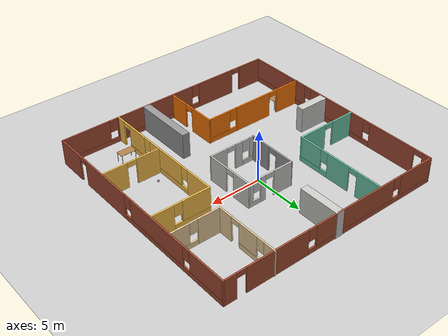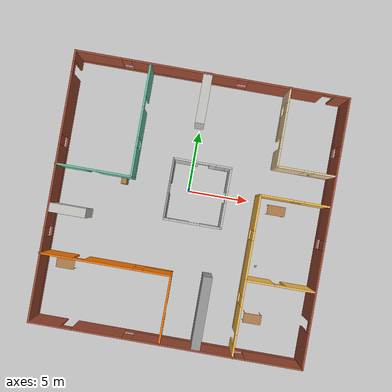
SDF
<sdf version="1.6">
 <world name="default">
  <light name="sun" type="directional">
   <pose>0 0 10 0 -0 0</pose>
   <diffuse>0.8 0.8 0.8 1</diffuse>
   <specular>0.2 0.2 0.2 1</specular>
   <attenuation>
    <range>1000</range>
    <constant>0.9</constant>
    <linear>0.01</linear>
    <quadratic>0.001</quadratic>
   </attenuation>
   <direction>-0.5 0.1 -0.9</direction>
  </light>
  <model name="ground_plane">
   <static>1</static>
   <link name="link">
    <collision name="collision">
     <geometry><plane><normal>0 0 1</normal><size>100 100</size></plane></geometry>
     <surface><friction><ode><mu>100</mu><mu2>50</mu2></ode></friction></surface>
    </collision>
    <visual name="visual">
     <cast_shadows>0</cast_shadows>
     <geometry><plane><normal>0 0 1</normal><size>100 100</size></plane></geometry>
     <material>
      <script><uri>file://media/materials/scripts/gazebo.material</uri><name>Gazebo/Grey</name></script>
     </material>
    </visual>
   </link>
  </model>
  <gravity>0 0 -9.8</gravity>
  <magnetic_field>6e-06 2.3e-05 -4.2e-05</magnetic_field>
  <atmosphere type="adiabatic"/>
  <physics name="default_physics" default="0" type="ode">
   <max_step_size>0.001</max_step_size>
   <real_time_factor>1</real_time_factor>
   <real_time_update_rate>1000</real_time_update_rate>
  </physics>
  <scene><ambient>0.4 0.4 0.4 1</ambient><background>0.7 0.7 0.7 1</background><shadows>1</shadows></scene>
  <audio><device>default</device></audio>
  <spherical_coordinates>
   <surface_model>EARTH_WGS84</surface_model>
   <latitude_deg>0</latitude_deg>
   <longitude_deg>0</longitude_deg>
   <elevation>0</elevation>
   <heading_deg>0</heading_deg>
  </spherical_coordinates>
  <model name="floor">
   <pose>0.248 -1.57026 0 0 -0 0</pose>
   <link name="Wall_24">
    <pose>-11.0156 -0.019394 0 0 -0 -1.5708</pose>
    <visual name="Wall_24_Visual_0">
     <pose>-10.5538 0 1.25 0 -0 0</pose>
     <geometry><box><size>0.892447 0.15 2.5</size></box></geometry>
     <material>
      <script><uri>file://media/materials/scripts/gazebo.material</uri><name>Gazebo/Bricks</name></script>
      <ambient>0.760784 0.662745 0.627451 1</ambient>
     </material>
     <meta><layer>0</layer></meta>
    </visual>
    <collision name="Wall_24_Collision_0">
     <geometry><box><size>0.892447 0.15 2.5</size></box></geometry>
     <pose>-10.5538 0 1.25 0 -0 0</pose>
    </collision>
    <visual name="Wall_24_Visual_1">
     <pose>-6.69897 0 1.25 0 -0 0</pose>
     <geometry><box><size>5.01718 0.15 2.5</size></box></geometry>
     <material>
      <script><uri>file://media/materials/scripts/gazebo.material</uri><name>Gazebo/Bricks</name></script>
      <ambient>0.760784 0.662745 0.627451 1</ambient>
     </material>
     <meta><layer>0</layer></meta>
    </visual>
    <collision name="Wall_24_Collision_1">
     <geometry><box><size>5.01718 0.15 2.5</size></box></geometry>
     <pose>-6.69897 0 1.25 0 -0 0</pose>
    </collision>
    <visual name="Wall_24_Visual_2">
     <pose>3.40481 0 0.25 0 -0 0</pose>
     <geometry><box><size>15.1904 0.15 0.5</size></box></geometry>
     <material>
      <script><uri>file://media/materials/scripts/gazebo.material</uri><name>Gazebo/Bricks</name></script>
      <ambient>0.760784 0.662745 0.627451 1</ambient>
     </material>
     <meta><layer>0</layer></meta>
    </visual>
    <collision name="Wall_24_Collision_2">
     <geometry><box><size>15.1904 0.15 0.5</size></box></geometry>
     <pose>3.40481 0 0.25 0 -0 0</pose>
    </collision>
    <visual name="Wall_24_Visual_3">
     <pose>-0.044953 0 1.5 0 -0 0</pose>
     <geometry><box><size>6.69085 0.15 2</size></box></geometry>
     <material>
      <script><uri>file://media/materials/scripts/gazebo.material</uri><name>Gazebo/Bricks</name></script>
      <ambient>0.760784 0.662745 0.627451 1</ambient>
     </material>
     <meta><layer>0</layer></meta>
    </visual>
    <collision name="Wall_24_Collision_3">
     <geometry><box><size>6.69085 0.15 2</size></box></geometry>
     <pose>-0.044953 0 1.5 0 -0 0</pose>
    </collision>
    <visual name="Wall_24_Visual_4">
     <pose>7.55023 0 1.5 0 -0 0</pose>
     <geometry><box><size>6.89953 0.15 2</size></box></geometry>
     <material>
      <script><uri>file://media/materials/scripts/gazebo.material</uri><name>Gazebo/Bricks</name></script>
      <ambient>0.760784 0.662745 0.627451 1</ambient>
     </material>
     <meta><layer>0</layer></meta>
    </visual>
    <collision name="Wall_24_Collision_4">
     <geometry><box><size>6.89953 0.15 2</size></box></geometry>
     <pose>7.55023 0 1.5 0 -0 0</pose>
    </collision>
    <visual name="Wall_24_Visual_5">
     <pose>-3.79038 0 1.9 0 -0 0</pose>
     <geometry><box><size>0.8 0.15 1.2</size></box></geometry>
     <material>
      <script><uri>file://media/materials/scripts/gazebo.material</uri><name>Gazebo/Bricks</name></script>
      <ambient>0.760784 0.662745 0.627451 1</ambient>
     </material>
     <meta><layer>0</layer></meta>
    </visual>
    <collision name="Wall_24_Collision_5">
     <geometry><box><size>0.8 0.15 1.2</size></box></geometry>
     <pose>-3.79038 0 1.9 0 -0 0</pose>
    </collision>
    <visual name="Wall_24_Visual_6">
     <pose>3.70047 0 1.9 0 -0 0</pose>
     <geometry><box><size>0.8 0.15 1.2</size></box></geometry>
     <material>
      <script><uri>file://media/materials/scripts/gazebo.material</uri><name>Gazebo/Bricks</name></script>
      <ambient>0.760784 0.662745 0.627451 1</ambient>
     </material>
     <meta><layer>0</layer></meta>
    </visual>
    <collision name="Wall_24_Collision_6">
     <geometry><box><size>0.8 0.15 1.2</size></box></geometry>
     <pose>3.70047 0 1.9 0 -0 0</pose>
    </collision>
    <visual name="Wall_24_Visual_7">
     <pose>-9.65755 0 2.25 0 -0 0</pose>
     <geometry><box><size>0.9 0.15 0.5</size></box></geometry>
     <material>
      <script><uri>file://media/materials/scripts/gazebo.material</uri><name>Gazebo/Bricks</name></script>
      <ambient>0.760784 0.662745 0.627451 1</ambient>
     </material>
     <meta><layer>0</layer></meta>
    </visual>
    <collision name="Wall_24_Collision_7">
     <geometry><box><size>0.9 0.15 0.5</size></box></geometry>
     <pose>-9.65755 0 2.25 0 -0 0</pose>
    </collision>
   </link>
   <link name="Wall_25">
    <pose>0.034373 -10.9444 0 0 -0 0</pose>
    <visual name="Wall_25_Visual_0">
     <pose>-9.80645 0 1.25 0 -0 0</pose>
     <geometry><box><size>2.63709 0.15 2.5</size></box></geometry>
     <material>
      <script><uri>file://media/materials/scripts/gazebo.material</uri><name>Gazebo/Bricks</name></script>
      <ambient>0.760784 0.662745 0.627451 1</ambient>
     </material>
     <meta><layer>0</layer></meta>
    </visual>
    <collision name="Wall_25_Collision_0">
     <geometry><box><size>2.63709 0.15 2.5</size></box></geometry>
     <pose>-9.80645 0 1.25 0 -0 0</pose>
    </collision>
    <visual name="Wall_25_Visual_1">
     <pose>-5.54747 0 1.25 0 -0 0</pose>
     <geometry><box><size>4.08088 0.15 2.5</size></box></geometry>
     <material>
      <script><uri>file://media/materials/scripts/gazebo.material</uri><name>Gazebo/Bricks</name></script>
      <ambient>0.760784 0.662745 0.627451 1</ambient>
     </material>
     <meta><layer>0</layer></meta>
    </visual>
    <collision name="Wall_25_Collision_1">
     <geometry><box><size>4.08088 0.15 2.5</size></box></geometry>
     <pose>-5.54747 0 1.25 0 -0 0</pose>
    </collision>
    <visual name="Wall_25_Visual_2">
     <pose>3.80898 0 0.25 0 -0 0</pose>
     <geometry><box><size>14.632 0.15 0.5</size></box></geometry>
     <material>
      <script><uri>file://media/materials/scripts/gazebo.material</uri><name>Gazebo/Bricks</name></script>
      <ambient>0.760784 0.662745 0.627451 1</ambient>
     </material>
     <meta><layer>0</layer></meta>
    </visual>
    <collision name="Wall_25_Collision_2">
     <geometry><box><size>14.632 0.15 0.5</size></box></geometry>
     <pose>3.80898 0 0.25 0 -0 0</pose>
    </collision>
    <visual name="Wall_25_Visual_3">
     <pose>1.44344 0 1.5 0 -0 0</pose>
     <geometry><box><size>8.30095 0.15 2</size></box></geometry>
     <material>
      <script><uri>file://media/materials/scripts/gazebo.material</uri><name>Gazebo/Bricks</name></script>
      <ambient>0.760784 0.662745 0.627451 1</ambient>
     </material>
     <meta><layer>0</layer></meta>
    </visual>
    <collision name="Wall_25_Collision_3">
     <geometry><box><size>8.30095 0.15 2</size></box></geometry>
     <pose>1.44344 0 1.5 0 -0 0</pose>
    </collision>
    <visual name="Wall_25_Visual_4">
     <pose>8.75946 0 1.5 0 -0 0</pose>
     <geometry><box><size>4.73108 0.15 2</size></box></geometry>
     <material>
      <script><uri>file://media/materials/scripts/gazebo.material</uri><name>Gazebo/Bricks</name></script>
      <ambient>0.760784 0.662745 0.627451 1</ambient>
     </material>
     <meta><layer>0</layer></meta>
    </visual>
    <collision name="Wall_25_Collision_4">
     <geometry><box><size>4.73108 0.15 2</size></box></geometry>
     <pose>8.75946 0 1.5 0 -0 0</pose>
    </collision>
    <visual name="Wall_25_Visual_5">
     <pose>-3.10703 0 1.9 0 -0 0</pose>
     <geometry><box><size>0.8 0.15 1.2</size></box></geometry>
     <material>
      <script><uri>file://media/materials/scripts/gazebo.material</uri><name>Gazebo/Bricks</name></script>
      <ambient>0.760784 0.662745 0.627451 1</ambient>
     </material>
     <meta><layer>0</layer></meta>
    </visual>
    <collision name="Wall_25_Collision_5">
     <geometry><box><size>0.8 0.15 1.2</size></box></geometry>
     <pose>-3.10703 0 1.9 0 -0 0</pose>
    </collision>
    <visual name="Wall_25_Visual_6">
     <pose>5.99392 0 1.9 0 -0 0</pose>
     <geometry><box><size>0.8 0.15 1.2</size></box></geometry>
     <material>
      <script><uri>file://media/materials/scripts/gazebo.material</uri><name>Gazebo/Bricks</name></script>
      <ambient>0.760784 0.662745 0.627451 1</ambient>
     </material>
     <meta><layer>0</layer></meta>
    </visual>
    <collision name="Wall_25_Collision_6">
     <geometry><box><size>0.8 0.15 1.2</size></box></geometry>
     <pose>5.99392 0 1.9 0 -0 0</pose>
    </collision>
    <visual name="Wall_25_Visual_7">
     <pose>-8.03791 0 2.25 0 -0 0</pose>
     <geometry><box><size>0.9 0.15 0.5</size></box></geometry>
     <material>
      <script><uri>file://media/materials/scripts/gazebo.material</uri><name>Gazebo/Bricks</name></script>
      <ambient>0.760784 0.662745 0.627451 1</ambient>
     </material>
     <meta><layer>0</layer></meta>
    </visual>
    <collision name="Wall_25_Collision_7">
     <geometry><box><size>0.9 0.15 0.5</size></box></geometry>
     <pose>-8.03791 0 2.25 0 -0 0</pose>
    </collision>
   </link>
   <link name="Wall_26">
    <pose>11.0844 -0.019394 0 0 -0 1.5708</pose>
    <visual name="Wall_26_Visual_0">
     <pose>-9.51526 0 1.25 0 -0 0</pose>
     <geometry><box><size>2.96947 0.15 2.5</size></box></geometry>
     <material>
      <script><uri>file://media/materials/scripts/gazebo.material</uri><name>Gazebo/Bricks</name></script>
      <ambient>1 0.764706 0.305882 1</ambient>
     </material>
     <meta><layer>0</layer></meta>
    </visual>
    <collision name="Wall_26_Collision_0">
     <geometry><box><size>2.96947 0.15 2.5</size></box></geometry>
     <pose>-9.51526 0 1.25 0 -0 0</pose>
    </collision>
    <visual name="Wall_26_Visual_1">
     <pose>-4.23534 0 1.25 0 -0 0</pose>
     <geometry><box><size>5.79037 0.15 2.5</size></box></geometry>
     <material>
      <script><uri>file://media/materials/scripts/gazebo.material</uri><name>Gazebo/Bricks</name></script>
      <ambient>1 0.764706 0.305882 1</ambient>
     </material>
     <meta><layer>0</layer></meta>
    </visual>
    <collision name="Wall_26_Collision_1">
     <geometry><box><size>5.79037 0.15 2.5</size></box></geometry>
     <pose>-4.23534 0 1.25 0 -0 0</pose>
    </collision>
    <visual name="Wall_26_Visual_2">
     <pose>4.82992 0 0.25 0 -0 0</pose>
     <geometry><box><size>12.3402 0.15 0.5</size></box></geometry>
     <material>
      <script><uri>file://media/materials/scripts/gazebo.material</uri><name>Gazebo/Bricks</name></script>
      <ambient>1 0.764706 0.305882 1</ambient>
     </material>
     <meta><layer>0</layer></meta>
    </visual>
    <collision name="Wall_26_Collision_2">
     <geometry><box><size>12.3402 0.15 0.5</size></box></geometry>
     <pose>4.82992 0 0.25 0 -0 0</pose>
    </collision>
    <visual name="Wall_26_Visual_3">
     <pose>2.88033 0 1.5 0 -0 0</pose>
     <geometry><box><size>6.84097 0.15 2</size></box></geometry>
     <material>
      <script><uri>file://media/materials/scripts/gazebo.material</uri><name>Gazebo/Bricks</name></script>
      <ambient>1 0.764706 0.305882 1</ambient>
     </material>
     <meta><layer>0</layer></meta>
    </visual>
    <collision name="Wall_26_Collision_3">
     <geometry><box><size>6.84097 0.15 2</size></box></geometry>
     <pose>2.88033 0 1.5 0 -0 0</pose>
    </collision>
    <visual name="Wall_26_Visual_4">
     <pose>9.05041 0 1.5 0 -0 0</pose>
     <geometry><box><size>3.89918 0.15 2</size></box></geometry>
     <material>
      <script><uri>file://media/materials/scripts/gazebo.material</uri><name>Gazebo/Bricks</name></script>
      <ambient>1 0.764706 0.305882 1</ambient>
     </material>
     <meta><layer>0</layer></meta>
    </visual>
    <collision name="Wall_26_Collision_4">
     <geometry><box><size>3.89918 0.15 2</size></box></geometry>
     <pose>9.05041 0 1.5 0 -0 0</pose>
    </collision>
    <visual name="Wall_26_Visual_5">
     <pose>-0.940157 0 1.9 0 -0 0</pose>
     <geometry><box><size>0.8 0.15 1.2</size></box></geometry>
     <material>
      <script><uri>file://media/materials/scripts/gazebo.material</uri><name>Gazebo/Bricks</name></script>
      <ambient>1 0.764706 0.305882 1</ambient>
     </material>
     <meta><layer>0</layer></meta>
    </visual>
    <collision name="Wall_26_Collision_5">
     <geometry><box><size>0.8 0.15 1.2</size></box></geometry>
     <pose>-0.940157 0 1.9 0 -0 0</pose>
    </collision>
    <visual name="Wall_26_Visual_6">
     <pose>6.70082 0 1.9 0 -0 0</pose>
     <geometry><box><size>0.8 0.15 1.2</size></box></geometry>
     <material>
      <script><uri>file://media/materials/scripts/gazebo.material</uri><name>Gazebo/Bricks</name></script>
      <ambient>1 0.764706 0.305882 1</ambient>
     </material>
     <meta><layer>0</layer></meta>
    </visual>
    <collision name="Wall_26_Collision_6">
     <geometry><box><size>0.8 0.15 1.2</size></box></geometry>
     <pose>6.70082 0 1.9 0 -0 0</pose>
    </collision>
    <visual name="Wall_26_Visual_7">
     <pose>-7.58053 0 2.25 0 -0 0</pose>
     <geometry><box><size>0.9 0.15 0.5</size></box></geometry>
     <material>
      <script><uri>file://media/materials/scripts/gazebo.material</uri><name>Gazebo/Bricks</name></script>
      <ambient>1 0.764706 0.305882 1</ambient>
     </material>
     <meta><layer>0</layer></meta>
    </visual>
    <collision name="Wall_26_Collision_7">
     <geometry><box><size>0.9 0.15 0.5</size></box></geometry>
     <pose>-7.58053 0 2.25 0 -0 0</pose>
    </collision>
   </link>
   <link name="Wall_27">
    <pose>0.034373 10.9056 0 0 -0 3.14159</pose>
    <visual name="Wall_27_Visual_0">
     <pose>-10.5011 0 1.25 0 -0 0</pose>
     <geometry><box><size>1.24782 0.15 2.5</size></box></geometry>
     <material>
      <script><uri>file://media/materials/scripts/gazebo.material</uri><name>Gazebo/Bricks</name></script>
      <ambient>1 0.764706 0.305882 1</ambient>
     </material>
     <meta><layer>0</layer></meta>
    </visual>
    <collision name="Wall_27_Collision_0">
     <geometry><box><size>1.24782 0.15 2.5</size></box></geometry>
     <pose>-10.5011 0 1.25 0 -0 0</pose>
    </collision>
    <visual name="Wall_27_Visual_1">
     <pose>-5.94146 0 1.25 0 -0 0</pose>
     <geometry><box><size>6.07144 0.15 2.5</size></box></geometry>
     <material>
      <script><uri>file://media/materials/scripts/gazebo.material</uri><name>Gazebo/Bricks</name></script>
      <ambient>1 0.764706 0.305882 1</ambient>
     </material>
     <meta><layer>0</layer></meta>
    </visual>
    <collision name="Wall_27_Collision_1">
     <geometry><box><size>6.07144 0.15 2.5</size></box></geometry>
     <pose>-5.94146 0 1.25 0 -0 0</pose>
    </collision>
    <visual name="Wall_27_Visual_2">
     <pose>4.10963 0 0.25 0 -0 0</pose>
     <geometry><box><size>14.0307 0.15 0.5</size></box></geometry>
     <material>
      <script><uri>file://media/materials/scripts/gazebo.material</uri><name>Gazebo/Bricks</name></script>
      <ambient>1 0.764706 0.305882 1</ambient>
     </material>
     <meta><layer>0</layer></meta>
    </visual>
    <collision name="Wall_27_Collision_2">
     <geometry><box><size>14.0307 0.15 0.5</size></box></geometry>
     <pose>4.10963 0 0.25 0 -0 0</pose>
    </collision>
    <visual name="Wall_27_Visual_3">
     <pose>2.21603 0 1.5 0 -0 0</pose>
     <geometry><box><size>8.64354 0.15 2</size></box></geometry>
     <material>
      <script><uri>file://media/materials/scripts/gazebo.material</uri><name>Gazebo/Bricks</name></script>
      <ambient>1 0.764706 0.305882 1</ambient>
     </material>
     <meta><layer>0</layer></meta>
    </visual>
    <collision name="Wall_27_Collision_3">
     <geometry><box><size>8.64354 0.15 2</size></box></geometry>
     <pose>2.21603 0 1.5 0 -0 0</pose>
    </collision>
    <visual name="Wall_27_Visual_4">
     <pose>9.2314 0 1.5 0 -0 0</pose>
     <geometry><box><size>3.7872 0.15 2</size></box></geometry>
     <material>
      <script><uri>file://media/materials/scripts/gazebo.material</uri><name>Gazebo/Bricks</name></script>
      <ambient>1 0.764706 0.305882 1</ambient>
     </material>
     <meta><layer>0</layer></meta>
    </visual>
    <collision name="Wall_27_Collision_4">
     <geometry><box><size>3.7872 0.15 2</size></box></geometry>
     <pose>9.2314 0 1.5 0 -0 0</pose>
    </collision>
    <visual name="Wall_27_Visual_5">
     <pose>-2.50574 0 1.9 0 -0 0</pose>
     <geometry><box><size>0.8 0.15 1.2</size></box></geometry>
     <material>
      <script><uri>file://media/materials/scripts/gazebo.material</uri><name>Gazebo/Bricks</name></script>
      <ambient>1 0.764706 0.305882 1</ambient>
     </material>
     <meta><layer>0</layer></meta>
    </visual>
    <collision name="Wall_27_Collision_5">
     <geometry><box><size>0.8 0.15 1.2</size></box></geometry>
     <pose>-2.50574 0 1.9 0 -0 0</pose>
    </collision>
    <visual name="Wall_27_Visual_6">
     <pose>6.9378 0 1.9 0 -0 0</pose>
     <geometry><box><size>0.8 0.15 1.2</size></box></geometry>
     <material>
      <script><uri>file://media/materials/scripts/gazebo.material</uri><name>Gazebo/Bricks</name></script>
      <ambient>1 0.764706 0.305882 1</ambient>
     </material>
     <meta><layer>0</layer></meta>
    </visual>
    <collision name="Wall_27_Collision_6">
     <geometry><box><size>0.8 0.15 1.2</size></box></geometry>
     <pose>6.9378 0 1.9 0 -0 0</pose>
    </collision>
    <visual name="Wall_27_Visual_7">
     <pose>-9.42718 0 2.25 0 -0 0</pose>
     <geometry><box><size>0.9 0.15 0.5</size></box></geometry>
     <material>
      <script><uri>file://media/materials/scripts/gazebo.material</uri><name>Gazebo/Bricks</name></script>
      <ambient>1 0.764706 0.305882 1</ambient>
     </material>
     <meta><layer>0</layer></meta>
    </visual>
    <collision name="Wall_27_Collision_7">
     <geometry><box><size>0.9 0.15 0.5</size></box></geometry>
     <pose>-9.42718 0 2.25 0 -0 0</pose>
    </collision>
   </link>
   <link name="Wall_35">
    <pose>6.33295 7.78232 0 0 -0 -1.5708</pose>
    <visual name="Wall_35_Visual_0">
     <pose>-2.62794 0 1.25 0 -0 0</pose>
     <geometry><box><size>1.24413 0.15 2.5</size></box></geometry>
     <material>
      <script><uri>file://media/materials/scripts/gazebo.material</uri><name>Gazebo/Grey</name></script>
      <ambient>0.921569 0.807843 0.615686 1</ambient>
     </material>
     <meta><layer>0</layer></meta>
    </visual>
    <collision name="Wall_35_Collision_0">
     <geometry><box><size>1.24413 0.15 2.5</size></box></geometry>
     <pose>-2.62794 0 1.25 0 -0 0</pose>
    </collision>
    <visual name="Wall_35_Visual_1">
     <pose>2.48543 0 1.25 0 -0 0</pose>
     <geometry><box><size>1.52914 0.15 2.5</size></box></geometry>
     <material>
      <script><uri>file://media/materials/scripts/gazebo.material</uri><name>Gazebo/Grey</name></script>
      <ambient>0.921569 0.807843 0.615686 1</ambient>
     </material>
     <meta><layer>0</layer></meta>
    </visual>
    <collision name="Wall_35_Collision_1">
     <geometry><box><size>1.52914 0.15 2.5</size></box></geometry>
     <pose>2.48543 0 1.25 0 -0 0</pose>
    </collision>
    <visual name="Wall_35_Visual_2">
     <pose>-0.592504 0 0.25 0 -0 0</pose>
     <geometry><box><size>2.82674 0.15 0.5</size></box></geometry>
     <material>
      <script><uri>file://media/materials/scripts/gazebo.material</uri><name>Gazebo/Grey</name></script>
      <ambient>0.921569 0.807843 0.615686 1</ambient>
     </material>
     <meta><layer>0</layer></meta>
    </visual>
    <collision name="Wall_35_Collision_2">
     <geometry><box><size>2.82674 0.15 0.5</size></box></geometry>
     <pose>-0.592504 0 0.25 0 -0 0</pose>
    </collision>
    <visual name="Wall_35_Visual_3">
     <pose>-0.192504 0 1.5 0 -0 0</pose>
     <geometry><box><size>2.02673 0.15 2</size></box></geometry>
     <material>
      <script><uri>file://media/materials/scripts/gazebo.material</uri><name>Gazebo/Grey</name></script>
      <ambient>0.921569 0.807843 0.615686 1</ambient>
     </material>
     <meta><layer>0</layer></meta>
    </visual>
    <collision name="Wall_35_Collision_3">
     <geometry><box><size>2.02673 0.15 2</size></box></geometry>
     <pose>-0.192504 0 1.5 0 -0 0</pose>
    </collision>
    <visual name="Wall_35_Visual_4">
     <pose>-1.60587 0 1.9 0 -0 0</pose>
     <geometry><box><size>0.8 0.15 1.2</size></box></geometry>
     <material>
      <script><uri>file://media/materials/scripts/gazebo.material</uri><name>Gazebo/Grey</name></script>
      <ambient>0.921569 0.807843 0.615686 1</ambient>
     </material>
     <meta><layer>0</layer></meta>
    </visual>
    <collision name="Wall_35_Collision_4">
     <geometry><box><size>0.8 0.15 1.2</size></box></geometry>
     <pose>-1.60587 0 1.9 0 -0 0</pose>
    </collision>
    <visual name="Wall_35_Visual_5">
     <pose>1.27086 0 2.25 0 -0 0</pose>
     <geometry><box><size>0.9 0.15 0.5</size></box></geometry>
     <material>
      <script><uri>file://media/materials/scripts/gazebo.material</uri><name>Gazebo/Grey</name></script>
      <ambient>0.921569 0.807843 0.615686 1</ambient>
     </material>
     <meta><layer>0</layer></meta>
    </visual>
    <collision name="Wall_35_Collision_5">
     <geometry><box><size>0.9 0.15 0.5</size></box></geometry>
     <pose>1.27086 0 2.25 0 -0 0</pose>
    </collision>
   </link>
   <link name="Wall_36">
    <pose>8.63295 4.60732 0 0 -0 0</pose>
    <visual name="Wall_36_Visual_0">
     <pose>-1.25605 0 1.25 0 -0 0</pose>
     <geometry><box><size>2.23791 0.15 2.5</size></box></geometry>
     <material>
      <script><uri>file://media/materials/scripts/gazebo.material</uri><name>Gazebo/Grey</name></script>
      <ambient>0.921569 0.807843 0.615686 1</ambient>
     </material>
     <meta><layer>0</layer></meta>
    </visual>
    <collision name="Wall_36_Collision_0">
     <geometry><box><size>2.23791 0.15 2.5</size></box></geometry>
     <pose>-1.25605 0 1.25 0 -0 0</pose>
    </collision>
    <visual name="Wall_36_Visual_1">
     <pose>1.11895 0 0.25 0 -0 0</pose>
     <geometry><box><size>2.51209 0.15 0.5</size></box></geometry>
     <material>
      <script><uri>file://media/materials/scripts/gazebo.material</uri><name>Gazebo/Grey</name></script>
      <ambient>0.921569 0.807843 0.615686 1</ambient>
     </material>
     <meta><layer>0</layer></meta>
    </visual>
    <collision name="Wall_36_Collision_1">
     <geometry><box><size>2.51209 0.15 0.5</size></box></geometry>
     <pose>1.11895 0 0.25 0 -0 0</pose>
    </collision>
    <visual name="Wall_36_Visual_2">
     <pose>1.51896 0 1.5 0 -0 0</pose>
     <geometry><box><size>1.71209 0.15 2</size></box></geometry>
     <material>
      <script><uri>file://media/materials/scripts/gazebo.material</uri><name>Gazebo/Grey</name></script>
      <ambient>0.921569 0.807843 0.615686 1</ambient>
     </material>
     <meta><layer>0</layer></meta>
    </visual>
    <collision name="Wall_36_Collision_2">
     <geometry><box><size>1.71209 0.15 2</size></box></geometry>
     <pose>1.51896 0 1.5 0 -0 0</pose>
    </collision>
    <visual name="Wall_36_Visual_3">
     <pose>0.26291 0 1.9 0 -0 0</pose>
     <geometry><box><size>0.8 0.15 1.2</size></box></geometry>
     <material>
      <script><uri>file://media/materials/scripts/gazebo.material</uri><name>Gazebo/Grey</name></script>
      <ambient>0.921569 0.807843 0.615686 1</ambient>
     </material>
     <meta><layer>0</layer></meta>
    </visual>
    <collision name="Wall_36_Collision_3">
     <geometry><box><size>0.8 0.15 1.2</size></box></geometry>
     <pose>0.26291 0 1.9 0 -0 0</pose>
    </collision>
   </link>
   <link name="Wall_38">
    <pose>-4.96477 6.35501 0 0 -0 -1.5708</pose>
    <visual name="Wall_38_Visual_0">
     <pose>-3.29568 0 1.25 0 -0 0</pose>
     <geometry><box><size>2.65865 0.15 2.5</size></box></geometry>
     <material>
      <script><uri>file://media/materials/scripts/gazebo.material</uri><name>Gazebo/Grey</name></script>
      <ambient>0.435294 0.796078 0.67451 1</ambient>
     </material>
     <meta><layer>0</layer></meta>
    </visual>
    <collision name="Wall_38_Collision_0">
     <geometry><box><size>2.65865 0.15 2.5</size></box></geometry>
     <pose>-3.29568 0 1.25 0 -0 0</pose>
    </collision>
    <visual name="Wall_38_Visual_1">
     <pose>0.156233 0 1.25 0 -0 0</pose>
     <geometry><box><size>2.44517 0.15 2.5</size></box></geometry>
     <material>
      <script><uri>file://media/materials/scripts/gazebo.material</uri><name>Gazebo/Grey</name></script>
      <ambient>0.435294 0.796078 0.67451 1</ambient>
     </material>
     <meta><layer>0</layer></meta>
    </visual>
    <collision name="Wall_38_Collision_1">
     <geometry><box><size>2.44517 0.15 2.5</size></box></geometry>
     <pose>0.156233 0 1.25 0 -0 0</pose>
    </collision>
    <visual name="Wall_38_Visual_2">
     <pose>3.00191 0 0.25 0 -0 0</pose>
     <geometry><box><size>3.24618 0.15 0.5</size></box></geometry>
     <material>
      <script><uri>file://media/materials/scripts/gazebo.material</uri><name>Gazebo/Grey</name></script>
      <ambient>0.435294 0.796078 0.67451 1</ambient>
     </material>
     <meta><layer>0</layer></meta>
    </visual>
    <collision name="Wall_38_Collision_2">
     <geometry><box><size>3.24618 0.15 0.5</size></box></geometry>
     <pose>3.00191 0 0.25 0 -0 0</pose>
    </collision>
    <visual name="Wall_38_Visual_3">
     <pose>3.40191 0 1.5 0 -0 0</pose>
     <geometry><box><size>2.44618 0.15 2</size></box></geometry>
     <material>
      <script><uri>file://media/materials/scripts/gazebo.material</uri><name>Gazebo/Grey</name></script>
      <ambient>0.435294 0.796078 0.67451 1</ambient>
     </material>
     <meta><layer>0</layer></meta>
    </visual>
    <collision name="Wall_38_Collision_3">
     <geometry><box><size>2.44618 0.15 2</size></box></geometry>
     <pose>3.40191 0 1.5 0 -0 0</pose>
    </collision>
    <visual name="Wall_38_Visual_4">
     <pose>1.77882 0 1.9 0 -0 0</pose>
     <geometry><box><size>0.8 0.15 1.2</size></box></geometry>
     <material>
      <script><uri>file://media/materials/scripts/gazebo.material</uri><name>Gazebo/Grey</name></script>
      <ambient>0.435294 0.796078 0.67451 1</ambient>
     </material>
     <meta><layer>0</layer></meta>
    </visual>
    <collision name="Wall_38_Collision_4">
     <geometry><box><size>0.8 0.15 1.2</size></box></geometry>
     <pose>1.77882 0 1.9 0 -0 0</pose>
    </collision>
    <visual name="Wall_38_Visual_5">
     <pose>-1.51635 0 2.25 0 -0 0</pose>
     <geometry><box><size>0.9 0.15 0.5</size></box></geometry>
     <material>
      <script><uri>file://media/materials/scripts/gazebo.material</uri><name>Gazebo/Grey</name></script>
      <ambient>0.435294 0.796078 0.67451 1</ambient>
     </material>
     <meta><layer>0</layer></meta>
    </visual>
    <collision name="Wall_38_Collision_5">
     <geometry><box><size>0.9 0.15 0.5</size></box></geometry>
     <pose>-1.51635 0 2.25 0 -0 0</pose>
    </collision>
   </link>
   <link name="Wall_39">
    <pose>-8.01477 1.80501 0 0 -0 3.14159</pose>
    <visual name="Wall_39_Visual_0">
     <pose>-1.69107 0 1.25 0 -0 0</pose>
     <geometry><box><size>2.86787 0.15 2.5</size></box></geometry>
     <material>
      <script><uri>file://media/materials/scripts/gazebo.material</uri><name>Gazebo/Grey</name></script>
      <ambient>0.435294 0.796078 0.67451 1</ambient>
     </material>
     <meta><layer>0</layer></meta>
    </visual>
    <collision name="Wall_39_Collision_0">
     <geometry><box><size>2.86787 0.15 2.5</size></box></geometry>
     <pose>-1.69107 0 1.25 0 -0 0</pose>
    </collision>
    <visual name="Wall_39_Visual_1">
     <pose>1.88393 0 1.25 0 -0 0</pose>
     <geometry><box><size>2.48213 0.15 2.5</size></box></geometry>
     <material>
      <script><uri>file://media/materials/scripts/gazebo.material</uri><name>Gazebo/Grey</name></script>
      <ambient>0.435294 0.796078 0.67451 1</ambient>
     </material>
     <meta><layer>0</layer></meta>
    </visual>
    <collision name="Wall_39_Collision_1">
     <geometry><box><size>2.48213 0.15 2.5</size></box></geometry>
     <pose>1.88393 0 1.25 0 -0 0</pose>
    </collision>
    <visual name="Wall_39_Visual_2">
     <pose>0.192865 0 2.25 0 -0 0</pose>
     <geometry><box><size>0.9 0.15 0.5</size></box></geometry>
     <material>
      <script><uri>file://media/materials/scripts/gazebo.material</uri><name>Gazebo/Grey</name></script>
      <ambient>0.435294 0.796078 0.67451 1</ambient>
     </material>
     <meta><layer>0</layer></meta>
    </visual>
    <collision name="Wall_39_Collision_2">
     <geometry><box><size>0.9 0.15 0.5</size></box></geometry>
     <pose>0.192865 0 2.25 0 -0 0</pose>
    </collision>
   </link>
   <link name="Wall_41">
    <pose>-5.78437 -5.41392 0 0 -0 0</pose>
    <visual name="Wall_41_Visual_0">
     <pose>-4.01952 0 1.25 0 -0 0</pose>
     <geometry><box><size>2.71095 0.15 2.5</size></box></geometry>
     <material>
      <script><uri>file://media/materials/scripts/gazebo.material</uri><name>Gazebo/Grey</name></script>
      <ambient>0.996078 0.47451 0.0196078 1</ambient>
     </material>
     <meta><layer>0</layer></meta>
    </visual>
    <collision name="Wall_41_Collision_0">
     <geometry><box><size>2.71095 0.15 2.5</size></box></geometry>
     <pose>-4.01952 0 1.25 0 -0 0</pose>
    </collision>
    <visual name="Wall_41_Visual_1">
     <pose>0.21695 0 1.25 0 -0 0</pose>
     <geometry><box><size>3.96199 0.15 2.5</size></box></geometry>
     <material>
      <script><uri>file://media/materials/scripts/gazebo.material</uri><name>Gazebo/Grey</name></script>
      <ambient>0.996078 0.47451 0.0196078 1</ambient>
     </material>
     <meta><layer>0</layer></meta>
    </visual>
    <collision name="Wall_41_Collision_1">
     <geometry><box><size>3.96199 0.15 2.5</size></box></geometry>
     <pose>0.21695 0 1.25 0 -0 0</pose>
    </collision>
    <visual name="Wall_41_Visual_2">
     <pose>3.78647 0 0.25 0 -0 0</pose>
     <geometry><box><size>3.17705 0.15 0.5</size></box></geometry>
     <material>
      <script><uri>file://media/materials/scripts/gazebo.material</uri><name>Gazebo/Grey</name></script>
      <ambient>0.996078 0.47451 0.0196078 1</ambient>
     </material>
     <meta><layer>0</layer></meta>
    </visual>
    <collision name="Wall_41_Collision_2">
     <geometry><box><size>3.17705 0.15 0.5</size></box></geometry>
     <pose>3.78647 0 0.25 0 -0 0</pose>
    </collision>
    <visual name="Wall_41_Visual_3">
     <pose>4.18647 0 1.5 0 -0 0</pose>
     <geometry><box><size>2.37705 0.15 2</size></box></geometry>
     <material>
      <script><uri>file://media/materials/scripts/gazebo.material</uri><name>Gazebo/Grey</name></script>
      <ambient>0.996078 0.47451 0.0196078 1</ambient>
     </material>
     <meta><layer>0</layer></meta>
    </visual>
    <collision name="Wall_41_Collision_3">
     <geometry><box><size>2.37705 0.15 2</size></box></geometry>
     <pose>4.18647 0 1.5 0 -0 0</pose>
    </collision>
    <visual name="Wall_41_Visual_4">
     <pose>2.59795 0 1.9 0 -0 0</pose>
     <geometry><box><size>0.8 0.15 1.2</size></box></geometry>
     <material>
      <script><uri>file://media/materials/scripts/gazebo.material</uri><name>Gazebo/Grey</name></script>
      <ambient>0.996078 0.47451 0.0196078 1</ambient>
     </material>
     <meta><layer>0</layer></meta>
    </visual>
    <collision name="Wall_41_Collision_4">
     <geometry><box><size>0.8 0.15 1.2</size></box></geometry>
     <pose>2.59795 0 1.9 0 -0 0</pose>
    </collision>
    <visual name="Wall_41_Visual_5">
     <pose>-2.21405 0 2.25 0 -0 0</pose>
     <geometry><box><size>0.9 0.15 0.5</size></box></geometry>
     <material>
      <script><uri>file://media/materials/scripts/gazebo.material</uri><name>Gazebo/Grey</name></script>
      <ambient>0.996078 0.47451 0.0196078 1</ambient>
     </material>
     <meta><layer>0</layer></meta>
    </visual>
    <collision name="Wall_41_Collision_5">
     <geometry><box><size>0.9 0.15 0.5</size></box></geometry>
     <pose>-2.21405 0 2.25 0 -0 0</pose>
    </collision>
   </link>
   <link name="Wall_42">
    <pose>-0.484375 -8.08892 0 0 -0 -1.5708</pose>
    <visual name="Wall_42_Visual_0">
     <pose>-1.44683 0 1.25 0 -0 0</pose>
     <geometry><box><size>2.60634 0.15 2.5</size></box></geometry>
     <material>
      <script><uri>file://media/materials/scripts/gazebo.material</uri><name>Gazebo/Grey</name></script>
      <ambient>0.996078 0.47451 0.0196078 1</ambient>
     </material>
     <meta><layer>0</layer></meta>
    </visual>
    <collision name="Wall_42_Collision_0">
     <geometry><box><size>2.60634 0.15 2.5</size></box></geometry>
     <pose>-1.44683 0 1.25 0 -0 0</pose>
    </collision>
    <visual name="Wall_42_Visual_1">
     <pose>1.75317 0 1.25 0 -0 0</pose>
     <geometry><box><size>1.99366 0.15 2.5</size></box></geometry>
     <material>
      <script><uri>file://media/materials/scripts/gazebo.material</uri><name>Gazebo/Grey</name></script>
      <ambient>0.996078 0.47451 0.0196078 1</ambient>
     </material>
     <meta><layer>0</layer></meta>
    </visual>
    <collision name="Wall_42_Collision_1">
     <geometry><box><size>1.99366 0.15 2.5</size></box></geometry>
     <pose>1.75317 0 1.25 0 -0 0</pose>
    </collision>
    <visual name="Wall_42_Visual_2">
     <pose>0.306344 0 2.25 0 -0 0</pose>
     <geometry><box><size>0.9 0.15 0.5</size></box></geometry>
     <material>
      <script><uri>file://media/materials/scripts/gazebo.material</uri><name>Gazebo/Grey</name></script>
      <ambient>0.996078 0.47451 0.0196078 1</ambient>
     </material>
     <meta><layer>0</layer></meta>
    </visual>
    <collision name="Wall_42_Collision_2">
     <geometry><box><size>0.9 0.15 0.5</size></box></geometry>
     <pose>0.306344 0 2.25 0 -0 0</pose>
    </collision>
   </link>
   <link name="Wall_49">
    <pose>0.463971 3.82841 0 0 -0 0</pose>
    <visual name="Wall_49_Visual_0">
     <pose>-1.36562 0 1.25 0 -0 0</pose>
     <geometry><box><size>2.01877 0.15 2.5</size></box></geometry>
     <material>
      <script><uri>file://media/materials/scripts/gazebo.material</uri><name>Gazebo/CeilingTiled</name></script>
      <ambient>1 1 1 1</ambient>
     </material>
     <meta><layer>0</layer></meta>
    </visual>
    <collision name="Wall_49_Collision_0">
     <geometry><box><size>2.01877 0.15 2.5</size></box></geometry>
     <pose>-1.36562 0 1.25 0 -0 0</pose>
    </collision>
    <visual name="Wall_49_Visual_1">
     <pose>0.806946 0 1.25 0 -0 0</pose>
     <geometry><box><size>0.526351 0.15 2.5</size></box></geometry>
     <material>
      <script><uri>file://media/materials/scripts/gazebo.material</uri><name>Gazebo/CeilingTiled</name></script>
      <ambient>1 1 1 1</ambient>
     </material>
     <meta><layer>0</layer></meta>
    </visual>
    <collision name="Wall_49_Collision_1">
     <geometry><box><size>0.526351 0.15 2.5</size></box></geometry>
     <pose>0.806946 0 1.25 0 -0 0</pose>
    </collision>
    <visual name="Wall_49_Visual_2">
     <pose>1.72256 0 0.25 0 -0 0</pose>
     <geometry><box><size>1.30488 0.15 0.5</size></box></geometry>
     <material>
      <script><uri>file://media/materials/scripts/gazebo.material</uri><name>Gazebo/CeilingTiled</name></script>
      <ambient>1 1 1 1</ambient>
     </material>
     <meta><layer>0</layer></meta>
    </visual>
    <collision name="Wall_49_Collision_2">
     <geometry><box><size>1.30488 0.15 0.5</size></box></geometry>
     <pose>1.72256 0 0.25 0 -0 0</pose>
    </collision>
    <visual name="Wall_49_Visual_3">
     <pose>2.12256 0 1.5 0 -0 0</pose>
     <geometry><box><size>0.504879 0.15 2</size></box></geometry>
     <material>
      <script><uri>file://media/materials/scripts/gazebo.material</uri><name>Gazebo/CeilingTiled</name></script>
      <ambient>1 1 1 1</ambient>
     </material>
     <meta><layer>0</layer></meta>
    </visual>
    <collision name="Wall_49_Collision_3">
     <geometry><box><size>0.504879 0.15 2</size></box></geometry>
     <pose>2.12256 0 1.5 0 -0 0</pose>
    </collision>
    <visual name="Wall_49_Visual_4">
     <pose>1.47012 0 1.9 0 -0 0</pose>
     <geometry><box><size>0.8 0.15 1.2</size></box></geometry>
     <material>
      <script><uri>file://media/materials/scripts/gazebo.material</uri><name>Gazebo/CeilingTiled</name></script>
      <ambient>1 1 1 1</ambient>
     </material>
     <meta><layer>0</layer></meta>
    </visual>
    <collision name="Wall_49_Collision_4">
     <geometry><box><size>0.8 0.15 1.2</size></box></geometry>
     <pose>1.47012 0 1.9 0 -0 0</pose>
    </collision>
    <visual name="Wall_49_Visual_5">
     <pose>0.093771 0 2.25 0 -0 0</pose>
     <geometry><box><size>0.9 0.15 0.5</size></box></geometry>
     <material>
      <script><uri>file://media/materials/scripts/gazebo.material</uri><name>Gazebo/CeilingTiled</name></script>
      <ambient>1 1 1 1</ambient>
     </material>
     <meta><layer>0</layer></meta>
    </visual>
    <collision name="Wall_49_Collision_5">
     <geometry><box><size>0.9 0.15 0.5</size></box></geometry>
     <pose>0.093771 0 2.25 0 -0 0</pose>
    </collision>
   </link>
   <link name="Wall_50">
    <pose>2.76397 1.40341 0 0 -0 -1.5708</pose>
    <visual name="Wall_50_Visual_0">
     <pose>-1.52035 0 1.25 0 -0 0</pose>
     <geometry><box><size>1.9593 0.15 2.5</size></box></geometry>
     <material>
      <script><uri>file://media/materials/scripts/gazebo.material</uri><name>Gazebo/CeilingTiled</name></script>
      <ambient>1 1 1 1</ambient>
     </material>
     <meta><layer>0</layer></meta>
    </visual>
    <collision name="Wall_50_Collision_0">
     <geometry><box><size>1.9593 0.15 2.5</size></box></geometry>
     <pose>-1.52035 0 1.25 0 -0 0</pose>
    </collision>
    <visual name="Wall_50_Visual_1">
     <pose>1.42965 0 1.25 0 -0 0</pose>
     <geometry><box><size>2.1407 0.15 2.5</size></box></geometry>
     <material>
      <script><uri>file://media/materials/scripts/gazebo.material</uri><name>Gazebo/CeilingTiled</name></script>
      <ambient>1 1 1 1</ambient>
     </material>
     <meta><layer>0</layer></meta>
    </visual>
    <collision name="Wall_50_Collision_1">
     <geometry><box><size>2.1407 0.15 2.5</size></box></geometry>
     <pose>1.42965 0 1.25 0 -0 0</pose>
    </collision>
    <visual name="Wall_50_Visual_2">
     <pose>-0.090702 0 2.25 0 -0 0</pose>
     <geometry><box><size>0.9 0.15 0.5</size></box></geometry>
     <material>
      <script><uri>file://media/materials/scripts/gazebo.material</uri><name>Gazebo/CeilingTiled</name></script>
      <ambient>1 1 1 1</ambient>
     </material>
     <meta><layer>0</layer></meta>
    </visual>
    <collision name="Wall_50_Collision_2">
     <geometry><box><size>0.9 0.15 0.5</size></box></geometry>
     <pose>-0.090702 0 2.25 0 -0 0</pose>
    </collision>
   </link>
   <link name="Wall_51">
    <pose>0.463971 -1.02159 0 0 -0 3.14159</pose>
    <visual name="Wall_51_Visual_0">
     <pose>-1.48912 0 1.25 0 -0 0</pose>
     <geometry><box><size>1.77176 0.15 2.5</size></box></geometry>
     <material>
      <script><uri>file://media/materials/scripts/gazebo.material</uri><name>Gazebo/CeilingTiled</name></script>
      <ambient>0.760784 0.662745 0.627451 1</ambient>
     </material>
     <meta><layer>0</layer></meta>
    </visual>
    <collision name="Wall_51_Collision_0">
     <geometry><box><size>1.77176 0.15 2.5</size></box></geometry>
     <pose>-1.48912 0 1.25 0 -0 0</pose>
    </collision>
    <visual name="Wall_51_Visual_1">
     <pose>0.668741 0 1.25 0 -0 0</pose>
     <geometry><box><size>0.743969 0.15 2.5</size></box></geometry>
     <material>
      <script><uri>file://media/materials/scripts/gazebo.material</uri><name>Gazebo/CeilingTiled</name></script>
      <ambient>0.760784 0.662745 0.627451 1</ambient>
     </material>
     <meta><layer>0</layer></meta>
    </visual>
    <collision name="Wall_51_Collision_1">
     <geometry><box><size>0.743969 0.15 2.5</size></box></geometry>
     <pose>0.668741 0 1.25 0 -0 0</pose>
    </collision>
    <visual name="Wall_51_Visual_2">
     <pose>1.70786 0 0.25 0 -0 0</pose>
     <geometry><box><size>1.33427 0.15 0.5</size></box></geometry>
     <material>
      <script><uri>file://media/materials/scripts/gazebo.material</uri><name>Gazebo/CeilingTiled</name></script>
      <ambient>0.760784 0.662745 0.627451 1</ambient>
     </material>
     <meta><layer>0</layer></meta>
    </visual>
    <collision name="Wall_51_Collision_2">
     <geometry><box><size>1.33427 0.15 0.5</size></box></geometry>
     <pose>1.70786 0 0.25 0 -0 0</pose>
    </collision>
    <visual name="Wall_51_Visual_3">
     <pose>2.10786 0 1.5 0 -0 0</pose>
     <geometry><box><size>0.534274 0.15 2</size></box></geometry>
     <material>
      <script><uri>file://media/materials/scripts/gazebo.material</uri><name>Gazebo/CeilingTiled</name></script>
      <ambient>0.760784 0.662745 0.627451 1</ambient>
     </material>
     <meta><layer>0</layer></meta>
    </visual>
    <collision name="Wall_51_Collision_3">
     <geometry><box><size>0.534274 0.15 2</size></box></geometry>
     <pose>2.10786 0 1.5 0 -0 0</pose>
    </collision>
    <visual name="Wall_51_Visual_4">
     <pose>1.44073 0 1.9 0 -0 0</pose>
     <geometry><box><size>0.8 0.15 1.2</size></box></geometry>
     <material>
      <script><uri>file://media/materials/scripts/gazebo.material</uri><name>Gazebo/CeilingTiled</name></script>
      <ambient>0.760784 0.662745 0.627451 1</ambient>
     </material>
     <meta><layer>0</layer></meta>
    </visual>
    <collision name="Wall_51_Collision_4">
     <geometry><box><size>0.8 0.15 1.2</size></box></geometry>
     <pose>1.44073 0 1.9 0 -0 0</pose>
    </collision>
    <visual name="Wall_51_Visual_5">
     <pose>-0.153243 0 2.25 0 -0 0</pose>
     <geometry><box><size>0.9 0.15 0.5</size></box></geometry>
     <material>
      <script><uri>file://media/materials/scripts/gazebo.material</uri><name>Gazebo/CeilingTiled</name></script>
      <ambient>0.760784 0.662745 0.627451 1</ambient>
     </material>
     <meta><layer>0</layer></meta>
    </visual>
    <collision name="Wall_51_Collision_5">
     <geometry><box><size>0.9 0.15 0.5</size></box></geometry>
     <pose>-0.153243 0 2.25 0 -0 0</pose>
    </collision>
   </link>
   <link name="Wall_52">
    <pose>-1.83603 1.40341 0 0 -0 1.5708</pose>
    <visual name="Wall_52_Visual_0">
     <pose>-1.41478 0 1.25 0 -0 0</pose>
     <geometry><box><size>2.17044 0.15 2.5</size></box></geometry>
     <material>
      <script><uri>file://media/materials/scripts/gazebo.material</uri><name>Gazebo/Grey</name></script>
      <ambient>1 1 1 1</ambient>
     </material>
     <meta><layer>0</layer></meta>
    </visual>
    <collision name="Wall_52_Collision_0">
     <geometry><box><size>2.17044 0.15 2.5</size></box></geometry>
     <pose>-1.41478 0 1.25 0 -0 0</pose>
    </collision>
    <visual name="Wall_52_Visual_1">
     <pose>1.53522 0 1.25 0 -0 0</pose>
     <geometry><box><size>1.92956 0.15 2.5</size></box></geometry>
     <material>
      <script><uri>file://media/materials/scripts/gazebo.material</uri><name>Gazebo/Grey</name></script>
      <ambient>1 1 1 1</ambient>
     </material>
     <meta><layer>0</layer></meta>
    </visual>
    <collision name="Wall_52_Collision_1">
     <geometry><box><size>1.92956 0.15 2.5</size></box></geometry>
     <pose>1.53522 0 1.25 0 -0 0</pose>
    </collision>
    <visual name="Wall_52_Visual_2">
     <pose>0.120438 0 2.25 0 -0 0</pose>
     <geometry><box><size>0.9 0.15 0.5</size></box></geometry>
     <material>
      <script><uri>file://media/materials/scripts/gazebo.material</uri><name>Gazebo/Grey</name></script>
      <ambient>1 1 1 1</ambient>
     </material>
     <meta><layer>0</layer></meta>
    </visual>
    <collision name="Wall_52_Collision_2">
     <geometry><box><size>0.9 0.15 0.5</size></box></geometry>
     <pose>0.120438 0 2.25 0 -0 0</pose>
    </collision>
   </link>
   <link name="Wall_54">
    <pose>8.23049 2.14268 0 0 -0 3.14159</pose>
    <visual name="Wall_54_Visual_0">
     <pose>-1.78675 0 1.25 0 -0 0</pose>
     <geometry><box><size>2.17651 0.15 2.5</size></box></geometry>
     <material>
      <script><uri>file://media/materials/scripts/gazebo.material</uri><name>Gazebo/Grey</name></script>
      <ambient>1 0.764706 0.305882 1</ambient>
     </material>
     <meta><layer>0</layer></meta>
    </visual>
    <collision name="Wall_54_Collision_0">
     <geometry><box><size>2.17651 0.15 2.5</size></box></geometry>
     <pose>-1.78675 0 1.25 0 -0 0</pose>
    </collision>
    <visual name="Wall_54_Visual_1">
     <pose>1.08825 0 0.25 0 -0 0</pose>
     <geometry><box><size>3.57349 0.15 0.5</size></box></geometry>
     <material>
      <script><uri>file://media/materials/scripts/gazebo.material</uri><name>Gazebo/Grey</name></script>
      <ambient>1 0.764706 0.305882 1</ambient>
     </material>
     <meta><layer>0</layer></meta>
    </visual>
    <collision name="Wall_54_Collision_1">
     <geometry><box><size>3.57349 0.15 0.5</size></box></geometry>
     <pose>1.08825 0 0.25 0 -0 0</pose>
    </collision>
    <visual name="Wall_54_Visual_2">
     <pose>1.48826 0 1.5 0 -0 0</pose>
     <geometry><box><size>2.77349 0.15 2</size></box></geometry>
     <material>
      <script><uri>file://media/materials/scripts/gazebo.material</uri><name>Gazebo/Grey</name></script>
      <ambient>1 0.764706 0.305882 1</ambient>
     </material>
     <meta><layer>0</layer></meta>
    </visual>
    <collision name="Wall_54_Collision_2">
     <geometry><box><size>2.77349 0.15 2</size></box></geometry>
     <pose>1.48826 0 1.5 0 -0 0</pose>
    </collision>
    <visual name="Wall_54_Visual_3">
     <pose>-0.298491 0 1.9 0 -0 0</pose>
     <geometry><box><size>0.8 0.15 1.2</size></box></geometry>
     <material>
      <script><uri>file://media/materials/scripts/gazebo.material</uri><name>Gazebo/Grey</name></script>
      <ambient>1 0.764706 0.305882 1</ambient>
     </material>
     <meta><layer>0</layer></meta>
    </visual>
    <collision name="Wall_54_Collision_3">
     <geometry><box><size>0.8 0.15 1.2</size></box></geometry>
     <pose>-0.298491 0 1.9 0 -0 0</pose>
    </collision>
   </link>
   <link name="Wall_55">
    <pose>5.43049 -4.40732 0 0 -0 -1.5708</pose>
    <visual name="Wall_55_Visual_0">
     <pose>-5.15015 0 1.25 0 -0 0</pose>
     <geometry><box><size>2.9497 0.15 2.5</size></box></geometry>
     <material>
      <script><uri>file://media/materials/scripts/gazebo.material</uri><name>Gazebo/Grey</name></script>
      <ambient>1 0.764706 0.305882 1</ambient>
     </material>
     <meta><layer>0</layer></meta>
    </visual>
    <collision name="Wall_55_Collision_0">
     <geometry><box><size>2.9497 0.15 2.5</size></box></geometry>
     <pose>-5.15015 0 1.25 0 -0 0</pose>
    </collision>
    <visual name="Wall_55_Visual_1">
     <pose>6.12968 0 1.25 0 -0 0</pose>
     <geometry><box><size>0.990647 0.15 2.5</size></box></geometry>
     <material>
      <script><uri>file://media/materials/scripts/gazebo.material</uri><name>Gazebo/Grey</name></script>
      <ambient>1 0.764706 0.305882 1</ambient>
     </material>
     <meta><layer>0</layer></meta>
    </visual>
    <collision name="Wall_55_Collision_1">
     <geometry><box><size>0.990647 0.15 2.5</size></box></geometry>
     <pose>6.12968 0 1.25 0 -0 0</pose>
    </collision>
    <visual name="Wall_55_Visual_2">
     <pose>0.529528 0 0.25 0 -0 0</pose>
     <geometry><box><size>8.40965 0.15 0.5</size></box></geometry>
     <material>
      <script><uri>file://media/materials/scripts/gazebo.material</uri><name>Gazebo/Grey</name></script>
      <ambient>1 0.764706 0.305882 1</ambient>
     </material>
     <meta><layer>0</layer></meta>
    </visual>
    <collision name="Wall_55_Collision_2">
     <geometry><box><size>8.40965 0.15 0.5</size></box></geometry>
     <pose>0.529528 0 0.25 0 -0 0</pose>
    </collision>
    <visual name="Wall_55_Visual_3">
     <pose>-0.614601 0 1.5 0 -0 0</pose>
     <geometry><box><size>4.52139 0.15 2</size></box></geometry>
     <material>
      <script><uri>file://media/materials/scripts/gazebo.material</uri><name>Gazebo/Grey</name></script>
      <ambient>1 0.764706 0.305882 1</ambient>
     </material>
     <meta><layer>0</layer></meta>
    </visual>
    <collision name="Wall_55_Collision_3">
     <geometry><box><size>4.52139 0.15 2</size></box></geometry>
     <pose>-0.614601 0 1.5 0 -0 0</pose>
    </collision>
    <visual name="Wall_55_Visual_4">
     <pose>3.59022 0 1.5 0 -0 0</pose>
     <geometry><box><size>2.28826 0.15 2</size></box></geometry>
     <material>
      <script><uri>file://media/materials/scripts/gazebo.material</uri><name>Gazebo/Grey</name></script>
      <ambient>1 0.764706 0.305882 1</ambient>
     </material>
     <meta><layer>0</layer></meta>
    </visual>
    <collision name="Wall_55_Collision_4">
     <geometry><box><size>2.28826 0.15 2</size></box></geometry>
     <pose>3.59022 0 1.5 0 -0 0</pose>
    </collision>
    <visual name="Wall_55_Visual_5">
     <pose>-3.2753 0 1.9 0 -0 0</pose>
     <geometry><box><size>0.8 0.15 1.2</size></box></geometry>
     <material>
      <script><uri>file://media/materials/scripts/gazebo.material</uri><name>Gazebo/Grey</name></script>
      <ambient>1 0.764706 0.305882 1</ambient>
     </material>
     <meta><layer>0</layer></meta>
    </visual>
    <collision name="Wall_55_Collision_5">
     <geometry><box><size>0.8 0.15 1.2</size></box></geometry>
     <pose>-3.2753 0 1.9 0 -0 0</pose>
    </collision>
    <visual name="Wall_55_Visual_6">
     <pose>2.0461 0 1.9 0 -0 0</pose>
     <geometry><box><size>0.8 0.15 1.2</size></box></geometry>
     <material>
      <script><uri>file://media/materials/scripts/gazebo.material</uri><name>Gazebo/Grey</name></script>
      <ambient>1 0.764706 0.305882 1</ambient>
     </material>
     <meta><layer>0</layer></meta>
    </visual>
    <collision name="Wall_55_Collision_6">
     <geometry><box><size>0.8 0.15 1.2</size></box></geometry>
     <pose>2.0461 0 1.9 0 -0 0</pose>
    </collision>
    <visual name="Wall_55_Visual_7">
     <pose>5.18435 0 2.25 0 -0 0</pose>
     <geometry><box><size>0.9 0.15 0.5</size></box></geometry>
     <material>
      <script><uri>file://media/materials/scripts/gazebo.material</uri><name>Gazebo/Grey</name></script>
      <ambient>1 0.764706 0.305882 1</ambient>
     </material>
     <meta><layer>0</layer></meta>
    </visual>
    <collision name="Wall_55_Collision_7">
     <geometry><box><size>0.9 0.15 0.5</size></box></geometry>
     <pose>5.18435 0 2.25 0 -0 0</pose>
    </collision>
   </link>
   <link name="Wall_57">
    <pose>8.23621 -4.7251 0 0 -0 0</pose>
    <visual name="Wall_57_Visual_0">
     <pose>-1.6753 0 1.25 0 -0 0</pose>
     <geometry><box><size>2.3994 0.15 2.5</size></box></geometry>
     <material>
      <script><uri>file://media/materials/scripts/gazebo.material</uri><name>Gazebo/Grey</name></script>
      <ambient>1 0.764706 0.305882 1</ambient>
     </material>
     <meta><layer>0</layer></meta>
    </visual>
    <collision name="Wall_57_Collision_0">
     <geometry><box><size>2.3994 0.15 2.5</size></box></geometry>
     <pose>-1.6753 0 1.25 0 -0 0</pose>
    </collision>
    <visual name="Wall_57_Visual_1">
     <pose>1.6497 0 1.25 0 -0 0</pose>
     <geometry><box><size>2.4506 0.15 2.5</size></box></geometry>
     <material>
      <script><uri>file://media/materials/scripts/gazebo.material</uri><name>Gazebo/Grey</name></script>
      <ambient>1 0.764706 0.305882 1</ambient>
     </material>
     <meta><layer>0</layer></meta>
    </visual>
    <collision name="Wall_57_Collision_1">
     <geometry><box><size>2.4506 0.15 2.5</size></box></geometry>
     <pose>1.6497 0 1.25 0 -0 0</pose>
    </collision>
    <visual name="Wall_57_Visual_2">
     <pose>-0.025599 0 2.25 0 -0 0</pose>
     <geometry><box><size>0.9 0.15 0.5</size></box></geometry>
     <material>
      <script><uri>file://media/materials/scripts/gazebo.material</uri><name>Gazebo/Grey</name></script>
      <ambient>1 0.764706 0.305882 1</ambient>
     </material>
     <meta><layer>0</layer></meta>
    </visual>
    <collision name="Wall_57_Collision_2">
     <geometry><box><size>0.9 0.15 0.5</size></box></geometry>
     <pose>-0.025599 0 2.25 0 -0 0</pose>
    </collision>
   </link>
   <link name="Wall_59">
    <collision name="Wall_59_Collision">
     <geometry><box><size>4.1 0.75 2.5</size></box></geometry>
     <pose>0 0 1.25 0 -0 0</pose>
    </collision>
    <visual name="Wall_59_Visual">
     <pose>0 0 1.25 0 -0 0</pose>
     <geometry><box><size>4.1 0.75 2.5</size></box></geometry>
     <material>
      <script><uri>file://media/materials/scripts/gazebo.material</uri><name>Gazebo/CeilingTiled</name></script>
      <ambient>1 1 1 1</ambient>
     </material>
     <meta><layer>0</layer></meta>
    </visual>
    <pose>-0.329426 8.96966 0 0 -0 -1.5708</pose>
   </link>
   <link name="Wall_61">
    <collision name="Wall_61_Collision">
     <geometry><box><size>3 0.75 2.5</size></box></geometry>
     <pose>0 0 1.25 0 -0 0</pose>
    </collision>
    <visual name="Wall_61_Visual">
     <pose>0 0 1.25 0 -0 0</pose>
     <geometry><box><size>3 0.75 2.5</size></box></geometry>
     <material>
      <script><uri>file://media/materials/scripts/gazebo.material</uri><name>Gazebo/CeilingTiled</name></script>
      <ambient>1 1 1 1</ambient>
     </material>
     <meta><layer>0</layer></meta>
    </visual>
    <pose>-9.48988 -1.68604 0 0 -0 0</pose>
   </link>
   <link name="Wall_63">
    <collision name="Wall_63_Collision">
     <geometry><box><size>6 0.75 2.5</size></box></geometry>
     <pose>0 0 1.25 0 -0 0</pose>
    </collision>
    <visual name="Wall_63_Visual">
     <pose>0 0 1.25 0 -0 0</pose>
     <geometry><box><size>6 0.75 2.5</size></box></geometry>
     <material>
      <script><uri>file://media/materials/scripts/gazebo.material</uri><name>Gazebo/Grey</name></script>
      <ambient>1 1 1 1</ambient>
     </material>
     <meta><layer>0</layer></meta>
    </visual>
    <pose>2.43615 -7.97618 0 0 -0 1.5708</pose>
   </link>
   <static>1</static>
  </model>
  <model name="table">
   <static>1</static>
   <link name="link">
    <collision name="surface">
     <pose>0 0 1 0 -0 0</pose>
     <geometry><box><size>1.5 0.8 0.03</size></box></geometry>
     <surface><friction><ode><mu>0.6</mu><mu2>0.6</mu2></ode></friction></surface>
    </collision>
    <visual name="visual1">
     <pose>0 0 1 0 -0 0</pose>
     <geometry><box><size>1.5 0.8 0.03</size></box></geometry>
     <material>
      <script><uri>file://media/materials/scripts/gazebo.material</uri><name>Gazebo/Wood</name></script>
     </material>
    </visual>
    <collision name="front_left_leg">
     <pose>0.68 0.38 0.5 0 -0 0</pose>
     <geometry><cylinder><radius>0.02</radius><length>1</length></cylinder></geometry>
    </collision>
    <visual name="front_left_leg">
     <pose>0.68 0.38 0.5 0 -0 0</pose>
     <geometry><cylinder><radius>0.02</radius><length>1</length></cylinder></geometry>
     <material>
      <script><uri>file://media/materials/scripts/gazebo.material</uri><name>Gazebo/Grey</name></script>
     </material>
    </visual>
    <collision name="front_right_leg">
     <pose>0.68 -0.38 0.5 0 -0 0</pose>
     <geometry><cylinder><radius>0.02</radius><length>1</length></cylinder></geometry>
    </collision>
    <visual name="front_right_leg">
     <pose>0.68 -0.38 0.5 0 -0 0</pose>
     <geometry><cylinder><radius>0.02</radius><length>1</length></cylinder></geometry>
     <material>
      <script><uri>file://media/materials/scripts/gazebo.material</uri><name>Gazebo/Grey</name></script>
     </material>
    </visual>
    <collision name="back_right_leg">
     <pose>-0.68 -0.38 0.5 0 -0 0</pose>
     <geometry><cylinder><radius>0.02</radius><length>1</length></cylinder></geometry>
    </collision>
    <visual name="back_right_leg">
     <pose>-0.68 -0.38 0.5 0 -0 0</pose>
     <geometry><cylinder><radius>0.02</radius><length>1</length></cylinder></geometry>
     <material>
      <script><uri>file://media/materials/scripts/gazebo.material</uri><name>Gazebo/Grey</name></script>
     </material>
    </visual>
    <collision name="back_left_leg">
     <pose>-0.68 0.38 0.5 0 -0 0</pose>
     <geometry><cylinder><radius>0.02</radius><length>1</length></cylinder></geometry>
    </collision>
    <visual name="back_left_leg">
     <pose>-0.68 0.38 0.5 0 -0 0</pose>
     <geometry><cylinder><radius>0.02</radius><length>1</length></cylinder></geometry>
     <material>
      <script><uri>file://media/materials/scripts/gazebo.material</uri><name>Gazebo/Grey</name></script>
     </material>
    </visual>
   </link>
   <pose>-9.01866 -7.68895 0 0 -0 0</pose>
  </model>
  <model name="table_0">
   <static>1</static>
   <link name="link">
    <collision name="surface">
     <pose>0 0 1 0 -0 0</pose>
     <geometry><box><size>1.5 0.8 0.03</size></box></geometry>
     <surface><friction><ode><mu>0.6</mu><mu2>0.6</mu2></ode></friction></surface>
    </collision>
    <visual name="visual1">
     <pose>0 0 1 0 -0 0</pose>
     <geometry><box><size>1.5 0.8 0.03</size></box></geometry>
     <material>
      <script><uri>file://media/materials/scripts/gazebo.material</uri><name>Gazebo/Wood</name></script>
     </material>
    </visual>
    <collision name="front_left_leg">
     <pose>0.68 0.38 0.5 0 -0 0</pose>
     <geometry><cylinder><radius>0.02</radius><length>1</length></cylinder></geometry>
    </collision>
    <visual name="front_left_leg">
     <pose>0.68 0.38 0.5 0 -0 0</pose>
     <geometry><cylinder><radius>0.02</radius><length>1</length></cylinder></geometry>
     <material>
      <script><uri>file://media/materials/scripts/gazebo.material</uri><name>Gazebo/Grey</name></script>
     </material>
    </visual>
    <collision name="front_right_leg">
     <pose>0.68 -0.38 0.5 0 -0 0</pose>
     <geometry><cylinder><radius>0.02</radius><length>1</length></cylinder></geometry>
    </collision>
    <visual name="front_right_leg">
     <pose>0.68 -0.38 0.5 0 -0 0</pose>
     <geometry><cylinder><radius>0.02</radius><length>1</length></cylinder></geometry>
     <material>
      <script><uri>file://media/materials/scripts/gazebo.material</uri><name>Gazebo/Grey</name></script>
     </material>
    </visual>
    <collision name="back_right_leg">
     <pose>-0.68 -0.38 0.5 0 -0 0</pose>
     <geometry><cylinder><radius>0.02</radius><length>1</length></cylinder></geometry>
    </collision>
    <visual name="back_right_leg">
     <pose>-0.68 -0.38 0.5 0 -0 0</pose>
     <geometry><cylinder><radius>0.02</radius><length>1</length></cylinder></geometry>
     <material>
      <script><uri>file://media/materials/scripts/gazebo.material</uri><name>Gazebo/Grey</name></script>
     </material>
    </visual>
    <collision name="back_left_leg">
     <pose>-0.68 0.38 0.5 0 -0 0</pose>
     <geometry><cylinder><radius>0.02</radius><length>1</length></cylinder></geometry>
    </collision>
    <visual name="back_left_leg">
     <pose>-0.68 0.38 0.5 0 -0 0</pose>
     <geometry><cylinder><radius>0.02</radius><length>1</length></cylinder></geometry>
     <material>
      <script><uri>file://media/materials/scripts/gazebo.material</uri><name>Gazebo/Grey</name></script>
     </material>
    </visual>
   </link>
   <pose>7.38953 -0.403821 0 0 -0 0</pose>
  </model>
  <model name="table_1">
   <static>1</static>
   <link name="link">
    <collision name="surface">
     <pose>0 0 1 0 -0 0</pose>
     <geometry><box><size>1.5 0.8 0.03</size></box></geometry>
     <surface><friction><ode><mu>0.6</mu><mu2>0.6</mu2></ode></friction></surface>
    </collision>
    <visual name="visual1">
     <pose>0 0 1 0 -0 0</pose>
     <geometry><box><size>1.5 0.8 0.03</size></box></geometry>
     <material>
      <script><uri>file://media/materials/scripts/gazebo.material</uri><name>Gazebo/Wood</name></script>
     </material>
    </visual>
    <collision name="front_left_leg">
     <pose>0.68 0.38 0.5 0 -0 0</pose>
     <geometry><cylinder><radius>0.02</radius><length>1</length></cylinder></geometry>
    </collision>
    <visual name="front_left_leg">
     <pose>0.68 0.38 0.5 0 -0 0</pose>
     <geometry><cylinder><radius>0.02</radius><length>1</length></cylinder></geometry>
     <material>
      <script><uri>file://media/materials/scripts/gazebo.material</uri><name>Gazebo/Grey</name></script>
     </material>
    </visual>
    <collision name="front_right_leg">
     <pose>0.68 -0.38 0.5 0 -0 0</pose>
     <geometry><cylinder><radius>0.02</radius><length>1</length></cylinder></geometry>
    </collision>
    <visual name="front_right_leg">
     <pose>0.68 -0.38 0.5 0 -0 0</pose>
     <geometry><cylinder><radius>0.02</radius><length>1</length></cylinder></geometry>
     <material>
      <script><uri>file://media/materials/scripts/gazebo.material</uri><name>Gazebo/Grey</name></script>
     </material>
    </visual>
    <collision name="back_right_leg">
     <pose>-0.68 -0.38 0.5 0 -0 0</pose>
     <geometry><cylinder><radius>0.02</radius><length>1</length></cylinder></geometry>
    </collision>
    <visual name="back_right_leg">
     <pose>-0.68 -0.38 0.5 0 -0 0</pose>
     <geometry><cylinder><radius>0.02</radius><length>1</length></cylinder></geometry>
     <material>
      <script><uri>file://media/materials/scripts/gazebo.material</uri><name>Gazebo/Grey</name></script>
     </material>
    </visual>
    <collision name="back_left_leg">
     <pose>-0.68 0.38 0.5 0 -0 0</pose>
     <geometry><cylinder><radius>0.02</radius><length>1</length></cylinder></geometry>
    </collision>
    <visual name="back_left_leg">
     <pose>-0.68 0.38 0.5 0 -0 0</pose>
     <geometry><cylinder><radius>0.02</radius><length>1</length></cylinder></geometry>
     <material>
      <script><uri>file://media/materials/scripts/gazebo.material</uri><name>Gazebo/Grey</name></script>
     </material>
    </visual>
   </link>
   <pose>6.98007 -9.54278 0 0 -0 0</pose>
  </model>
  <model name="cabinet">
   <static>1</static>
   <link name="cabinet_bottom_plate">
    <inertial>
     <pose>0 0 -1 0 -0 0</pose>
     <inertia><ixx>2.05</ixx><ixy>0</ixy><ixz>0</ixz><iyy>2.05</iyy><iyz>0</iyz><izz>2.05</izz></inertia>
     <mass>25</mass>
    </inertial>
    <collision name="cabinet_bottom_plate_geom">
     <pose>0 0 0.01 0 -0 0</pose>
     <geometry><box><size>0.45 0.45 0.02</size></box></geometry>
    </collision>
    <visual name="cabinet_bottom_plate_geom_visual">
     <pose>0 0 0.01 0 -0 0</pose>
     <geometry><box><size>0.45 0.45 0.02</size></box></geometry>
     <material>
      <script><uri>file://media/materials/scripts/gazebo.material</uri><name>Gazebo/Wood</name></script>
     </material>
    </visual>
    <collision name="cabinet_bottom_plate_geom_cabinet_back_plate">
     <pose>0.235 0 0.51 0 -0 0</pose>
     <geometry><box><size>0.02 0.45 1.02</size></box></geometry>
    </collision>
    <visual name="cabinet_bottom_plate_geom_cabinet_back_plate_visual">
     <pose>0.235 0 0.51 0 -0 0</pose>
     <geometry><box><size>0.02 0.45 1.02</size></box></geometry>
     <material>
      <script><uri>file://media/materials/scripts/gazebo.material</uri><name>Gazebo/Wood</name></script>
     </material>
    </visual>
    <collision name="cabinet_bottom_plate_geom_cabinet_left_plate">
     <pose>0 0.235 0.51 0 -0 0</pose>
     <geometry><box><size>0.45 0.02 1.02</size></box></geometry>
    </collision>
    <visual name="cabinet_bottom_plate_geom_cabinet_left_plate_visual">
     <pose>0 0.235 0.51 0 -0 0</pose>
     <geometry><box><size>0.45 0.02 1.02</size></box></geometry>
     <material>
      <script><uri>file://media/materials/scripts/gazebo.material</uri><name>Gazebo/Wood</name></script>
     </material>
    </visual>
    <collision name="cabinet_bottom_plate_geom_cabinet_middle_plate">
     <pose>0 0 0.51 0 -0 0</pose>
     <geometry><box><size>0.45 0.45 0.02</size></box></geometry>
    </collision>
    <visual name="cabinet_bottom_plate_geom_cabinet_middle_plate_visual">
     <pose>0 0 0.51 0 -0 0</pose>
     <geometry><box><size>0.45 0.45 0.02</size></box></geometry>
     <material>
      <script><uri>file://media/materials/scripts/gazebo.material</uri><name>Gazebo/Wood</name></script>
     </material>
    </visual>
    <collision name="cabinet_bottom_plate_geom_cabinet_right_plate">
     <pose>0 -0.235 0.51 0 -0 0</pose>
     <geometry><box><size>0.45 0.02 1.02</size></box></geometry>
    </collision>
    <visual name="cabinet_bottom_plate_geom_cabinet_right_plate_visual">
     <pose>0 -0.235 0.51 0 -0 0</pose>
     <geometry><box><size>0.45 0.02 1.02</size></box></geometry>
     <material>
      <script><uri>file://media/materials/scripts/gazebo.material</uri><name>Gazebo/Wood</name></script>
     </material>
    </visual>
    <collision name="cabinet_bottom_plate_geom_cabinet_top_plate">
     <pose>0 0 1.01 0 -0 0</pose>
     <geometry><box><size>0.45 0.45 0.02</size></box></geometry>
    </collision>
    <visual name="cabinet_bottom_plate_geom_cabinet_top_plate_visual">
     <pose>0 0 1.01 0 -0 0</pose>
     <geometry><box><size>0.45 0.45 0.02</size></box></geometry>
     <material>
      <script><uri>file://media/materials/scripts/gazebo.material</uri><name>Gazebo/Wood</name></script>
     </material>
    </visual>
   </link>
   <pose>-5.43176 -0.125003 0 0 -0 0</pose>
  </model>
  <model name="my_ball">
   <link name="link_0">
    <inertial>
     <mass>1</mass>
     <inertia><ixx>0.1</ixx><ixy>0</ixy><ixz>0</ixz><iyy>0.1</iyy><iyz>0</iyz><izz>0.1</izz></inertia>
    </inertial>
    <visual name="visual">
     <geometry><sphere><radius>0.1</radius></sphere></geometry>
     <material>
      <lighting>1</lighting>
      <script><uri>file://media/materials/scripts/gazebo.material</uri><name>Gazebo/Grey</name></script>
      <shader type="vertex"><normal_map>__default__</normal_map></shader>
      <ambient>1 1 1 1</ambient>
      <diffuse>1 1 1 1</diffuse>
      <specular>1 1 1 1</specular>
      <emissive>0 0 0 1</emissive>
     </material>
    </visual>
    <collision name="collision">
     <geometry><sphere><radius>0.1</radius></sphere></geometry>
     <surface>
      <friction>
       <ode><mu>1</mu><mu2>1</mu2><fdir1>0 0 0</fdir1><slip1>0</slip1><slip2>0</slip2></ode>
       <torsional>
        <coefficient>1</coefficient>
        <patch_radius>0</patch_radius>
        <surface_radius>0</surface_radius>
        <use_patch_radius>1</use_patch_radius>
        <ode><slip>0</slip></ode>
       </torsional>
      </friction>
      <bounce><restitution_coefficient>0</restitution_coefficient><threshold>1e+06</threshold></bounce>
      <contact>
       <collide_without_contact>0</collide_without_contact>
       <collide_without_contact_bitmask>1</collide_without_contact_bitmask>
       <collide_bitmask>1</collide_bitmask>
       <ode>
        <soft_cfm>0</soft_cfm>
        <soft_erp>0.2</soft_erp>
        <kp>1e+13</kp>
        <kd>1</kd>
        <max_vel>0.01</max_vel>
        <min_depth>0</min_depth>
       </ode>
       <bullet>
        <split_impulse>1</split_impulse>
        <split_impulse_penetration_threshold>-0.01</split_impulse_penetration_threshold>
        <soft_cfm>0</soft_cfm>
        <soft_erp>0.2</soft_erp>
        <kp>1e+13</kp>
        <kd>1</kd>
       </bullet>
      </contact>
     </surface>
    </collision>
   </link>
   <static>0</static>
   <pose>6.64561 -5.29396 0.1 0 -0 0</pose>
  </model>
  <plugin filename="libcollision_map_creator.so" name="collision_map_creator"/>
 </world>
</sdf>
